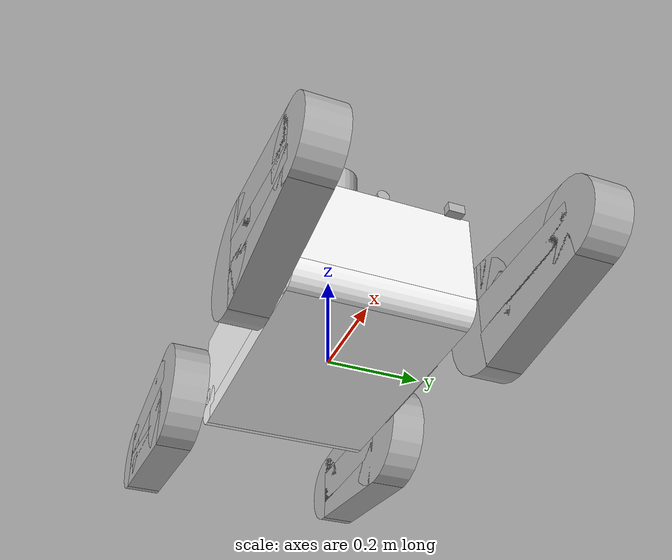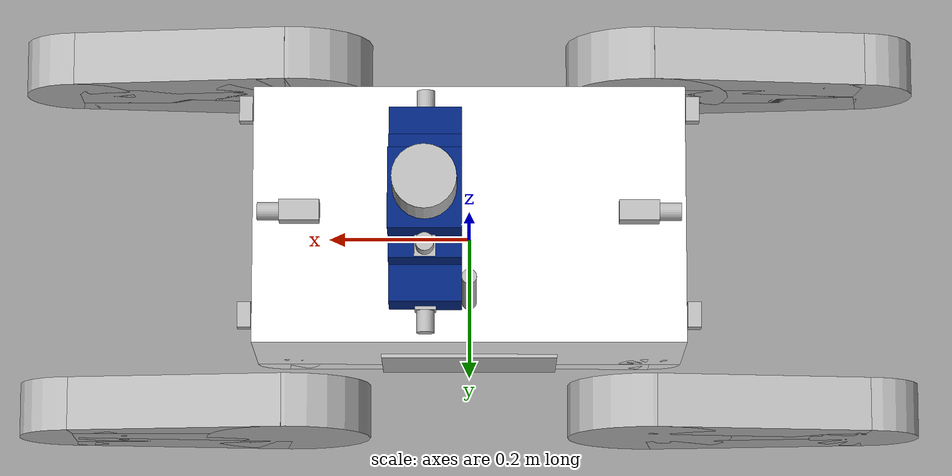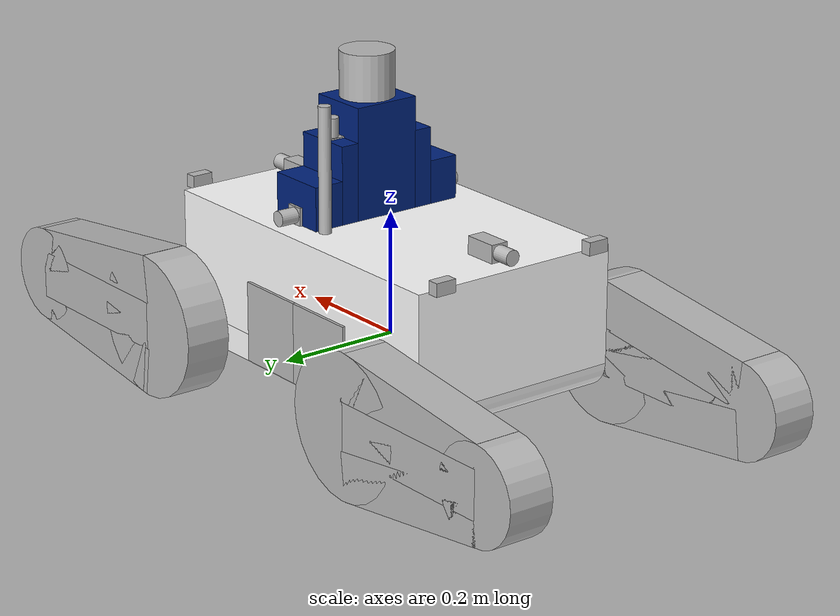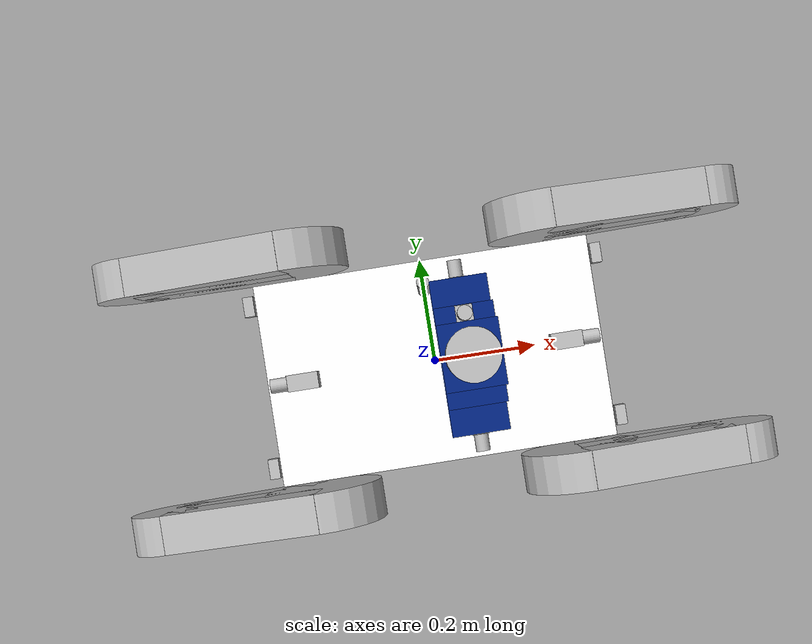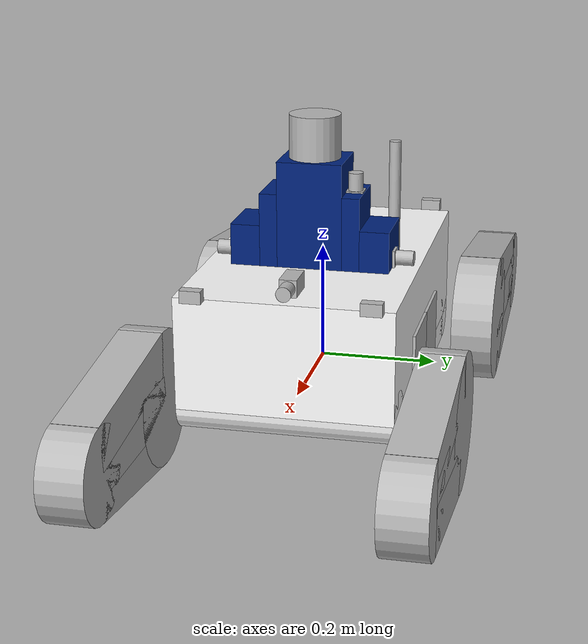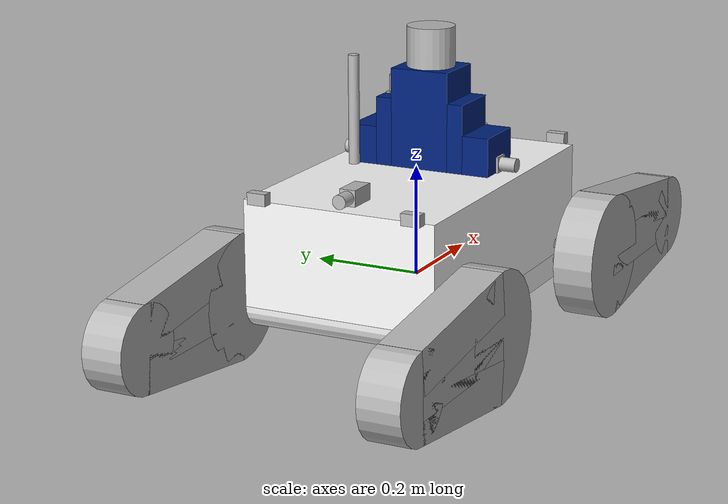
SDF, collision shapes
<?xml version='1.0' encoding='utf-8'?>
<sdf version="1.6">
  <model name="marv">
    <link name="base_link">
      <inertial>
        <pose>0 0 0.0661 0 -0 0</pose>
        <mass>8.7</mass>
        <inertia>
          <ixx>0.12905</ixx>
          <ixy>0</ixy>
          <ixz>0</ixz>
          <iyy>0.29609</iyy>
          <iyz>0</iyz>
          <izz>0.35496</izz>
        </inertia>
      </inertial>
      <collision name="base_link_collision">
        <pose>0 0 0.0961 0 -0 0</pose>
        <geometry>
          <box>
            <size>0.6 0.36 0.192</size>
          </box>
        </geometry>
      </collision>
      <collision name="base_link_collision_1">
        <pose>0 0 -0.0219 0 -0 0</pose>
        <geometry>
          <box>
            <size>0.512 0.36 0.044</size>
          </box>
        </geometry>
      </collision>
      <collision name="base_link_collision_2">
        <pose>0.256 0 0.000144 1.5707963267948966 -0 0</pose>
        <geometry>
          <cylinder>
            <length>0.36</length>
            <radius>0.044044</radius>
          </cylinder>
        </geometry>
      </collision>
      <collision name="base_link_collision_3">
        <pose>-0.256 0 0.000144 1.5707963267948966 -0 0</pose>
        <geometry>
          <cylinder>
            <length>0.36</length>
            <radius>0.044044</radius>
          </cylinder>
        </geometry>
      </collision>
      <visual name="base_link_fixed_joint_lump__chassis_visual">
        <material>
          <diffuse>1 1 1 1</diffuse>
          <pbr>
            <metal>
              <albedo_map>#{path}/textures/chassis.png</albedo_map>
              <emissive_map>#{path}/textures/chassis_emissive.png</emissive_map>
            </metal>
          </pbr>
        </material>
        <geometry>
          <mesh>
            <uri>#{path}/meshes/chassis.dae</uri>
          </mesh>
        </geometry>
      </visual>
      <visual name="base_link_visual_1">

        <pose>0 0 0.1841 0 -0 0</pose>
        <geometry>
          <mesh>
            <uri>#{path}/meshes/deck.dae</uri>
          </mesh>
        </geometry>
      </visual>
      <visual name="base_link_visual_2">

        <pose>0.256 0.18 0 0 -0 0</pose>
        <geometry>
          <mesh>
            <uri>#{path}/meshes/motor_housing.dae</uri>
          </mesh>
        </geometry>
      </visual>
      <visual name="base_link_visual_3">

        <pose>0.256 -0.18 0 0 -0 0</pose>
        <geometry>
          <mesh>
            <uri>#{path}/meshes/motor_housing_mirrored.dae</uri>
          </mesh>
        </geometry>
      </visual>
      <visual name="base_link_visual_4">

        <pose>-0.256 0.18 0 0 -0 0</pose>
        <geometry>
          <mesh>
            <scale>-1 -1 1</scale>
            <uri>#{path}/meshes/motor_housing_mirrored.dae</uri>
          </mesh>
        </geometry>
      </visual>
      <visual name="base_link_visual_5">
        <pose>-0.256 -0.18 0 0 -0 0</pose>
        <geometry>
          <mesh>
            <scale>-1 -1 1</scale>
            <uri>#{path}/meshes/motor_housing.dae</uri>
          </mesh>
        </geometry>
      </visual>
      <self_collide>0</self_collide>
      <light name="light_left" type="spot">
       <visualize>false</visualize>
        <pose>0 0.18 0.1621 1.5707963267948966 1.5707963267948966 0</pose>
        <cast_shadows>1</cast_shadows>
        <attenuation>
          <range>30</range>
          <linear>0.2</linear>
          <constant>0.1</constant>
          <quadratic>0.0025</quadratic>
        </attenuation>
        <diffuse>0.8 0.8 0.5 1</diffuse>
        <specular>0.8 0.8 0.5 1</specular>
        <spot>
          <inner_angle>2.8</inner_angle>
          <outer_angle>2.9</outer_angle>
          <falloff>1</falloff>
        </spot>
        <direction>1 0 0</direction>
      </light>
      <light name="light_right" type="spot">
       <visualize>false</visualize>
        <pose>0 -0.18 0.1621 -1.5707963267948966 1.5707963267948966 0</pose>
        <cast_shadows>1</cast_shadows>
        <attenuation>
          <range>30</range>
          <linear>0.2</linear>
          <constant>0.1</constant>
          <quadratic>0.0025</quadratic>
        </attenuation>
        <diffuse>0.8 0.8 0.5 1</diffuse>
        <specular>0.8 0.8 0.5 1</specular>
        <spot>
          <inner_angle>2.8</inner_angle>
          <outer_angle>2.9</outer_angle>
          <falloff>1</falloff>
        </spot>
        <direction>1 0 0</direction>
      </light>
      <light name="light_front" type="spot">
       <visualize>false</visualize>
        <pose>0.3 0 0.1621 -3.1415926535897931 1.5707963267948966 0</pose>
        <cast_shadows>1</cast_shadows>
        <attenuation>
          <range>30</range>
          <linear>0.2</linear>
          <constant>0.1</constant>
          <quadratic>0.0025</quadratic>
        </attenuation>
        <diffuse>0.8 0.8 0.5 1</diffuse>
        <specular>0.8 0.8 0.5 1</specular>
        <spot>
          <inner_angle>2.8</inner_angle>
          <outer_angle>2.9</outer_angle>
          <falloff>1</falloff>
        </spot>
        <direction>1 0 0</direction>
      </light>
      <light name="light_rear" type="spot">
       <visualize>false</visualize>
        <pose>-0.3 0 0.1621 0 1.5707963267948966 0</pose>
        <cast_shadows>1</cast_shadows>
        <attenuation>
          <range>40</range>
          <linear>0</linear>
          <constant>0.2</constant>
          <quadratic>0.0025</quadratic>
        </attenuation>
        <diffuse>0.8 0.8 0.5 1</diffuse>
        <specular>0.8 0.8 0.5 1</specular>
        <spot>
          <inner_angle>2.8</inner_angle>
          <outer_angle>2.9</outer_angle>
          <falloff>1</falloff>
        </spot>
        <direction>1 0 0</direction>
      </light>
    </link>
    <link name="battery1">
      <pose>0.06 0.005 0.0251 0 -0 0</pose>
      <inertial>
        <mass>6</mass>
        <inertia>
          <ixx>0.07325</ixx>
          <ixy>0</ixy>
          <ixz>0</ixz>
          <iyy>0.016388</iyy>
          <iyz>0</iyz>
          <izz>0.072738</izz>
        </inertia>
      </inertial>
      <collision name="battery1_collision">
        <geometry>
          <box>
            <size>0.126 0.36 0.13</size>
          </box>
        </geometry>
      </collision>
      <visual name="battery1_visual">
        <geometry>
          <mesh>
            <uri>#{path}/meshes/battery.dae</uri>
          </mesh>
        </geometry>
      </visual>
    </link>
    <joint name="battery1_j" type="fixed">
      <child>battery1</child>
      <parent>base_link</parent>
      <axis>
        <dynamics>
          <spring_reference>0</spring_reference>
          <spring_stiffness>0</spring_stiffness>
        </dynamics>
        <xyz>0 0 1</xyz>
        <use_parent_model_frame>0</use_parent_model_frame>
        <limit>
          <lower>-1e+16</lower>
          <upper>1e+16</upper>
        </limit>
      </axis>
      <physics>
        <ode>
          <limit>
            <cfm>0</cfm>
            <erp>0.2</erp>
          </limit>
        </ode>
      </physics>
    </joint>
    <link name="battery2">
      <pose>-0.06 0.005 0.0251 0 -0 0</pose>
      <inertial>
        <mass>6</mass>
        <inertia>
          <ixx>0.07325</ixx>
          <ixy>0</ixy>
          <ixz>0</ixz>
          <iyy>0.016388</iyy>
          <iyz>0</iyz>
          <izz>0.072738</izz>
        </inertia>
      </inertial>
      <collision name="battery2_collision">
        <geometry>
          <box>
            <size>0.126 0.36 0.13</size>
          </box>
        </geometry>
      </collision>
      <visual name="battery2_visual">
        <geometry>
          <mesh>
            <uri>#{path}/meshes/battery.dae</uri>
          </mesh>
        </geometry>
      </visual>
    </link>
    <joint name="battery2_j" type="fixed">
      <child>battery2</child>
      <parent>base_link</parent>
      <axis>
        <dynamics>
          <spring_reference>0</spring_reference>
          <spring_stiffness>0</spring_stiffness>
        </dynamics>
        <xyz>0 0 1</xyz>
        <use_parent_model_frame>0</use_parent_model_frame>
        <limit>
          <lower>-1e+16</lower>
          <upper>1e+16</upper>
        </limit>
      </axis>
      <physics>
        <ode>
          <limit>
            <cfm>0</cfm>
            <erp>0.2</erp>
          </limit>
        </ode>
      </physics>
    </joint>
    <link name="bottom_plate">
      <inertial>
        <pose>0 0 -0.0439 0 -0 0</pose>
        <mass>1.09</mass>
        <inertia>
          <ixx>0.0117743</ixx>
          <ixy>0</ixy>
          <ixz>0</ixz>
          <iyy>0.0327023</iyy>
          <iyz>0</iyz>
          <izz>0.044472</izz>
        </inertia>
      </inertial>
    </link>
    <joint name="bottom_plate_j" type="fixed">
      <child>bottom_plate</child>
      <parent>base_link</parent>
      <axis>
        <dynamics>
          <spring_reference>0</spring_reference>
          <spring_stiffness>0</spring_stiffness>
        </dynamics>
        <xyz>0 0 1</xyz>
        <use_parent_model_frame>0</use_parent_model_frame>
        <limit>
          <lower>-1e+16</lower>
          <upper>1e+16</upper>
        </limit>
      </axis>
      <physics>
        <ode>
          <limit>
            <cfm>0</cfm>
            <erp>0.2</erp>
          </limit>
        </ode>
      </physics>
    </joint>
    <link name="deck">
      <inertial>
        <pose>0 0 0.1921 0 -0 0</pose>
        <mass>3.4</mass>
        <inertia>
          <ixx>0.0367925</ixx>
          <ixy>0</ixy>
          <ixz>0</ixz>
          <iyy>0.102073</iyy>
          <iyz>0</iyz>
          <izz>0.13872</izz>
        </inertia>
      </inertial>
    </link>
    <joint name="deck_j" type="fixed">
      <child>deck</child>
      <parent>base_link</parent>
      <axis>
        <dynamics>
          <spring_reference>0</spring_reference>
          <spring_stiffness>0</spring_stiffness>
        </dynamics>
        <xyz>0 0 1</xyz>
        <use_parent_model_frame>0</use_parent_model_frame>
        <limit>
          <lower>-1e+16</lower>
          <upper>1e+16</upper>
        </limit>
      </axis>
      <physics>
        <ode>
          <limit>
            <cfm>0</cfm>
            <erp>0.2</erp>
          </limit>
        </ode>
      </physics>
    </joint>
    <link name="front_cam">
      <pose>0.244 0 0.1321 0 -0 0</pose>
      <inertial>
        <pose>0.019862 0 0.0145 0 -0 0</pose>
        <mass>0.14</mass>
        <inertia>
          <ixx>1.96233e-05</ixx>
          <ixy>0</ixy>
          <ixz>0</ixz>
          <iyy>6.75088e-05</iyy>
          <iyz>0</iyz>
          <izz>6.75088e-05</izz>
        </inertia>
      </inertial>
      <collision name="front_cam_collision_collision">
        <pose>0.0117 0 0.0145 0 -0 0</pose>
        <geometry>
          <box>
            <size>0.054 0.029 0.029</size>
          </box>
        </geometry>
      </collision>
      <collision name="front_cam_lens_collision_collision_1">
        <pose>0.042024 0 0.0145 0 1.5707963267948966 0</pose>
        <geometry>
          <cylinder>
            <length>0.026</length>
            <radius>0.0125</radius>
          </cylinder>
        </geometry>
      </collision>
      <visual name="front_cam_visual">
        <pose>0 0 0.0145 0 -0 0</pose>
        <geometry>
          <mesh>
            <uri>#{path}/meshes/basler_ace.dae</uri>
          </mesh>
        </geometry>
      </visual>
      <visual name="front_cam_visual_1">
        <pose>0.029024 0 0.0145 0 -0 0</pose>
        <geometry>
          <mesh>
            <uri>#{path}/meshes/evetar_fisheye_lens.dae</uri>
          </mesh>
        </geometry>
      </visual>
      <sensor name="front_cam" type="camera">
        <pose>0.051574 0 0.0145 0 -0 0</pose>
        <update_rate>15</update_rate>
        <camera>
          <horizontal_fov>2.40855</horizontal_fov>
          <image>
            <width>2048</width>
            <height>1536</height>
            <format>R8G8B8</format>
          </image>
          <clip>
            <near>0.025</near>
            <far>300</far>
          </clip>
          <noise>
            <type>gaussian</type>
            <mean>0</mean>
            <stddev>0.007</stddev>
          </noise>
          <lens>
            <intrinsics>
              <fx>393.077</fx>
              <fy>393.077</fy>
              <cx>1023.5</cx>
              <cy>767.5</cy>
              <s>0</s>
            </intrinsics>
            <type>stereographic</type>
            <scale_to_hfov>1</scale_to_hfov>
          </lens>
        </camera>
      </sensor>
    </link>
    <joint name="front_cam_j" type="fixed">
      <child>front_cam</child>
      <parent>base_link</parent>
      <axis>
        <dynamics>
          <spring_reference>0</spring_reference>
          <spring_stiffness>0</spring_stiffness>
        </dynamics>
        <xyz>0 0 1</xyz>
        <use_parent_model_frame>0</use_parent_model_frame>
        <limit>
          <lower>-1e+16</lower>
          <upper>1e+16</upper>
        </limit>
      </axis>
      <physics>
        <ode>
          <limit>
            <cfm>0</cfm>
            <erp>0.2</erp>
          </limit>
        </ode>
      </physics>
    </joint>
    <link name="front_left_flipper">
      <pose>0.256 0.248 0 0 -0 0</pose>
      <inertial>
        <mass>1e-05</mass>
        <inertia>
          <ixx>0.001</ixx>
          <ixy>1e-06</ixy>
          <ixz>1e-06</ixz>
          <iyy>0.001</iyy>
          <iyz>1e-06</iyz>
          <izz>0.001</izz>
        </inertia>
      </inertial>
      <collision name="front_left_flipper_collision">
          <pose>0.15175 0 0 0 -0 0</pose>
          <geometry>
            <box>
              <size>0.3035 0.075 0.078</size>
            </box>
          </geometry>
          <surface>
            <friction>
              <ode>
                <mu>1</mu>
                <mu2>150</mu2>
                <fdir1>0 0 1</fdir1>
              </ode>
            </friction>
          </surface>
        </collision>
        <collision name="front_left_flipper_collision_1">
          <pose>0.15175 0 0.05825 0 0.126179 0</pose>
          <geometry>
            <box>
              <size>0.3035 0.075 0.078</size>
            </box>
          </geometry>
          <surface>
            <friction>
              <ode>
                <mu>1</mu>
                <mu2>150</mu2>
                <fdir1>0 0 1</fdir1>
              </ode>
            </friction>
          </surface>
        </collision>
        <collision name="front_left_flipper_collision_2">
          <pose>0.15175 0 -0.05825 0 -0.126179 0</pose>
          <geometry>
            <box>
              <size>0.3035 0.075 0.078</size>
            </box>
          </geometry>
          <surface>
            <friction>
              <ode>
                <mu>1</mu>
                <mu2>150</mu2>
                <fdir1>0 0 1</fdir1>
              </ode>
            </friction>
          </surface>
        </collision>
        <collision name="front_left_flipper_collision_3">
          <pose>0.3035 0 0 1.5707963267948966 -0 0</pose>
          <geometry>
            <cylinder>
              <length>0.075</length>
              <radius>0.078</radius>
            </cylinder>
          </geometry>
          <surface>
            <friction>
              <ode>
                <mu>1</mu>
                <mu2>150</mu2>
                <fdir1>0 0 1</fdir1>
              </ode>
            </friction>
          </surface>
        </collision>
        <collision name="front_left_flipper_collision_4">
          <pose>0 0 0 1.5707963267948966 -0 0</pose>
          <geometry>
            <cylinder>
              <length>0.075</length>
              <radius>0.1165</radius>
            </cylinder>
          </geometry>
          <surface>
            <friction>
              <ode>
                <mu>1</mu>
                <mu2>150</mu2>
                <fdir1>0 0 1</fdir1>
              </ode>
            </friction>
          </surface>
        </collision>
      <visual name="front_left_flipper_visual">

        <geometry>
          <mesh>
            <uri>#{path}/meshes/big_wheel.dae</uri>
          </mesh>
        </geometry>
      </visual>
      <visual name="front_left_flipper_visual_1">

        <geometry>
          <mesh>
            <scale>-1 -1 1</scale>
            <uri>#{path}/meshes/flipper_arm.dae</uri>
          </mesh>
        </geometry>
      </visual>
      <visual name="front_left_flipper_visual_2">

        <geometry>
          <mesh>
            <uri>#{path}/meshes/belt.dae</uri>
          </mesh>
        </geometry>
      </visual>
      <visual name="front_left_flipper_visual_3">

        <pose>0.3035 0 0 0 -0 0</pose>
        <geometry>
          <mesh>
            <uri>#{path}/meshes/small_wheel.dae</uri>
          </mesh>
        </geometry>
      </visual>
      <self_collide>1</self_collide>
    </link>
    <joint name="front_left_flipper_j" type="revolute">
      <child>front_left_flipper</child>
      <parent>base_link</parent>
      <axis>
        <xyz>0 1 0</xyz>
        <limit>
          <lower>-1e+16</lower>
          <upper>1e+16</upper>
          <effort>240</effort>
          <velocity>5</velocity>
        </limit>
        <dynamics>
          <spring_reference>0</spring_reference>
          <spring_stiffness>0</spring_stiffness>
        </dynamics>
        <use_parent_model_frame>0</use_parent_model_frame>
      </axis>
      <physics>
        <ode>
          <implicit_spring_damper>1</implicit_spring_damper>
          <cfm_damping>1</cfm_damping>
          <limit>
            <cfm>0</cfm>
            <erp>0.2</erp>
          </limit>
        </ode>
      </physics>
    </joint>
    <link name="front_left_flipper_end_point_inflated">
      <pose>0.6375 0.248 0 0 -0 0</pose>
      <inertial>
        <mass>1e-05</mass>
        <inertia>
          <ixx>0.001</ixx>
          <ixy>1e-06</ixy>
          <ixz>1e-06</ixz>
          <iyy>0.001</iyy>
          <iyz>1e-06</iyz>
          <izz>0.001</izz>
        </inertia>
      </inertial>
    </link>
    <joint name="front_left_flipper_end_point_inflated_j" type="fixed">
      <child>front_left_flipper_end_point_inflated</child>
      <parent>front_left_flipper</parent>
      <axis>
        <dynamics>
          <spring_reference>0</spring_reference>
          <spring_stiffness>0</spring_stiffness>
        </dynamics>
        <xyz>0 0 1</xyz>
        <use_parent_model_frame>0</use_parent_model_frame>
        <limit>
          <lower>-1e+16</lower>
          <upper>1e+16</upper>
        </limit>
      </axis>
      <physics>
        <ode>
          <limit>
            <cfm>0</cfm>
            <erp>0.2</erp>
          </limit>
        </ode>
      </physics>
    </joint>
    <link name="front_left_flipper_end_point">
      <pose>0.6375 0.248 0 0 -0 0</pose>
      <inertial>
        <mass>1e-05</mass>
        <inertia>
          <ixx>0.001</ixx>
          <ixy>1e-06</ixy>
          <ixz>1e-06</ixz>
          <iyy>0.001</iyy>
          <iyz>1e-06</iyz>
          <izz>0.001</izz>
        </inertia>
      </inertial>
    </link>
    <joint name="front_left_flipper_end_point_j" type="fixed">
      <child>front_left_flipper_end_point</child>
      <parent>front_left_flipper</parent>
      <axis>
        <dynamics>
          <spring_reference>0</spring_reference>
          <spring_stiffness>0</spring_stiffness>
        </dynamics>
        <xyz>0 0 1</xyz>
        <use_parent_model_frame>0</use_parent_model_frame>
        <limit>
          <lower>-1e+16</lower>
          <upper>1e+16</upper>
        </limit>
      </axis>
      <physics>
        <ode>
          <limit>
            <cfm>0</cfm>
            <erp>0.2</erp>
          </limit>
        </ode>
      </physics>
    </joint>
    <link name="front_left_motor">
      <inertial>
        <pose>0.22 -0.09 0.02 0 -0 0</pose>
        <mass>4.06</mass>
        <inertia>
          <ixx>0.0151492</ixx>
          <ixy>0</ixy>
          <ixz>0</ixz>
          <iyy>0.0129839</iyy>
          <iyz>0</iyz>
          <izz>0.0173903</izz>
        </inertia>
      </inertial>
    </link>
    <joint name="front_left_motor_j" type="fixed">
      <child>front_left_motor</child>
      <parent>base_link</parent>
      <axis>
        <dynamics>
          <spring_reference>0</spring_reference>
          <spring_stiffness>0</spring_stiffness>
        </dynamics>
        <xyz>0 0 1</xyz>
        <use_parent_model_frame>0</use_parent_model_frame>
        <limit>
          <lower>-1e+16</lower>
          <upper>1e+16</upper>
        </limit>
      </axis>
      <physics>
        <ode>
          <limit>
            <cfm>0</cfm>
            <erp>0.2</erp>
          </limit>
        </ode>
      </physics>
    </joint>
    <link name="front_right_flipper">
      <pose>0.256 -0.248 0 3.1415926535897931 -0 -3.1415926535897931</pose>
      <inertial>
        <mass>1e-05</mass>
        <inertia>
          <ixx>0.001</ixx>
          <ixy>1e-06</ixy>
          <ixz>1e-06</ixz>
          <iyy>0.001</iyy>
          <iyz>1e-06</iyz>
          <izz>0.001</izz>
        </inertia>
      </inertial>
      <collision name="front_right_flipper_collision">
          <pose>-0.15175 0 0 0 -0 0</pose>
          <geometry>
            <box>
              <size>0.3035 0.075 0.078</size>
            </box>
          </geometry>
          <surface>
            <friction>
              <ode>
                <mu>1</mu>
                <mu2>150</mu2>
                <fdir1>0 0 1</fdir1>
              </ode>
            </friction>
          </surface>
        </collision>
        <collision name="front_right_flipper_collision_1">
          <pose>-0.15175 0 0.05825 0 -0.126179 0</pose>
          <geometry>
            <box>
              <size>0.3035 0.075 0.078</size>
            </box>
          </geometry>
          <surface>
            <friction>
              <ode>
                <mu>1</mu>
                <mu2>150</mu2>
                <fdir1>0 0 1</fdir1>
              </ode>
            </friction>
          </surface>
        </collision>
        <collision name="front_right_flipper_collision_2">
          <pose>-0.15175 0 -0.05825 0 0.126179 0</pose>
          <geometry>
            <box>
              <size>0.3035 0.075 0.078</size>
            </box>
          </geometry>
          <surface>
            <friction>
              <ode>
                <mu>1</mu>
                <mu2>150</mu2>
                <fdir1>0 0 1</fdir1>
              </ode>
            </friction>
          </surface>
        </collision>
        <collision name="front_right_flipper_collision_3">
          <pose>-0.3035 0 0 1.5707963267948966 -0 0</pose>
          <geometry>
            <cylinder>
              <length>0.075</length>
              <radius>0.078</radius>
            </cylinder>
          </geometry>
          <surface>
            <friction>
              <ode>
                <mu>1</mu>
                <mu2>150</mu2>
                <fdir1>0 0 1</fdir1>
              </ode>
            </friction>
          </surface>
        </collision>
        <collision name="front_right_flipper_collision_4">
          <pose>0 0 0 1.5707963267948966 -0 0</pose>
          <geometry>
            <cylinder>
              <length>0.075</length>
              <radius>0.1165</radius>
            </cylinder>
          </geometry>
          <surface>
            <friction>
              <ode>
                <mu>1</mu>
                <mu2>150</mu2>
                <fdir1>0 0 1</fdir1>
              </ode>
            </friction>
          </surface>
        </collision>
      <visual name="front_right_flipper_visual">
        <geometry>
          <mesh>
            <uri>#{path}/meshes/big_wheel.dae</uri>
          </mesh>
        </geometry>
      </visual>
      <visual name="front_right_flipper_visual_1">
        <geometry>
          <mesh>
            <uri>#{path}/meshes/flipper_arm.dae</uri>
          </mesh>
        </geometry>
      </visual>
      <visual name="front_right_flipper_visual_2">
        <pose>0 0 0 3.1415926535897931 -0 3.1415926535897931</pose>
        <geometry>
          <mesh>
            <uri>#{path}/meshes/belt.dae</uri>
          </mesh>
        </geometry>
      </visual>
      <visual name="front_right_flipper_visual_3">
        <pose>-0.3035 0 0 0 -0 0</pose>
        <geometry>
          <mesh>
            <uri>#{path}/meshes/small_wheel.dae</uri>
          </mesh>
        </geometry>
      </visual>
      <self_collide>1</self_collide>
    </link>
    <joint name="front_right_flipper_j" type="revolute">
      <child>front_right_flipper</child>
      <parent>base_link</parent>
      <axis>
        <xyz>0 1 0</xyz>
        <limit>
          <lower>-1e+16</lower>
          <upper>1e+16</upper>
          <effort>240</effort>
          <velocity>5</velocity>
        </limit>
        <dynamics>
          <spring_reference>0</spring_reference>
          <spring_stiffness>0</spring_stiffness>
        </dynamics>
        <use_parent_model_frame>0</use_parent_model_frame>
      </axis>
      <physics>
        <ode>
          <implicit_spring_damper>1</implicit_spring_damper>
          <cfm_damping>1</cfm_damping>
          <limit>
            <cfm>0</cfm>
            <erp>0.2</erp>
          </limit>
        </ode>
      </physics>
    </joint>
    <link name="front_right_flipper_end_point_inflated">
      <pose>0.6375 -0.248 -0 3.1415926535897931 -0 3.1415926535897931</pose>
      <inertial>
        <mass>1e-05</mass>
        <inertia>
          <ixx>0.001</ixx>
          <ixy>1e-06</ixy>
          <ixz>1e-06</ixz>
          <iyy>0.001</iyy>
          <iyz>1e-06</iyz>
          <izz>0.001</izz>
        </inertia>
      </inertial>
    </link>
    <joint name="front_right_flipper_end_point_inflated_j" type="fixed">
      <child>front_right_flipper_end_point_inflated</child>
      <parent>front_right_flipper</parent>
      <axis>
        <dynamics>
          <spring_reference>0</spring_reference>
          <spring_stiffness>0</spring_stiffness>
        </dynamics>
        <xyz>0 0 1</xyz>
        <use_parent_model_frame>0</use_parent_model_frame>
        <limit>
          <lower>-1e+16</lower>
          <upper>1e+16</upper>
        </limit>
      </axis>
      <physics>
        <ode>
          <limit>
            <cfm>0</cfm>
            <erp>0.2</erp>
          </limit>
        </ode>
      </physics>
    </joint>
    <link name="front_right_flipper_end_point">
      <pose>0.6375 -0.248 -0 3.1415926535897931 -0 3.1415926535897931</pose>
      <inertial>
        <mass>1e-05</mass>
        <inertia>
          <ixx>0.001</ixx>
          <ixy>1e-06</ixy>
          <ixz>1e-06</ixz>
          <iyy>0.001</iyy>
          <iyz>1e-06</iyz>
          <izz>0.001</izz>
        </inertia>
      </inertial>
    </link>
    <joint name="front_right_flipper_end_point_j" type="fixed">
      <child>front_right_flipper_end_point</child>
      <parent>front_right_flipper</parent>
      <axis>
        <dynamics>
          <spring_reference>0</spring_reference>
          <spring_stiffness>0</spring_stiffness>
        </dynamics>
        <xyz>0 0 1</xyz>
        <use_parent_model_frame>0</use_parent_model_frame>
        <limit>
          <lower>-1e+16</lower>
          <upper>1e+16</upper>
        </limit>
      </axis>
      <physics>
        <ode>
          <limit>
            <cfm>0</cfm>
            <erp>0.2</erp>
          </limit>
        </ode>
      </physics>
    </joint>
    <link name="front_right_motor">
      <inertial>
        <pose>0.22 0.09 0.02 0 -0 0</pose>
        <mass>4.06</mass>
        <inertia>
          <ixx>0.0151492</ixx>
          <ixy>0</ixy>
          <ixz>0</ixz>
          <iyy>0.0129839</iyy>
          <iyz>0</iyz>
          <izz>0.0173903</izz>
        </inertia>
      </inertial>
    </link>
    <joint name="front_right_motor_j" type="fixed">
      <child>front_right_motor</child>
      <parent>base_link</parent>
      <axis>
        <dynamics>
          <spring_reference>0</spring_reference>
          <spring_stiffness>0</spring_stiffness>
        </dynamics>
        <xyz>0 0 1</xyz>
        <use_parent_model_frame>0</use_parent_model_frame>
        <limit>
          <lower>-1e+16</lower>
          <upper>1e+16</upper>
        </limit>
      </axis>
      <physics>
        <ode>
          <limit>
            <cfm>0</cfm>
            <erp>0.2</erp>
          </limit>
        </ode>
      </physics>
    </joint>
    <link name="imu">
      <pose>0 0 0.15 -3.1415926535897931 0 0</pose>
      <inertial>
        <mass>1e-05</mass>
        <inertia>
          <ixx>0.001</ixx>
          <ixy>1e-06</ixy>
          <ixz>1e-06</ixz>
          <iyy>0.001</iyy>
          <iyz>1e-06</iyz>
          <izz>0.001</izz>
        </inertia>
      </inertial>
      <self_collide>0</self_collide>
      <sensor name="imu" type="imu">
        <always_on>1</always_on>
        <update_rate>50</update_rate>
        <imu>
          <angular_velocity>
            <x>
              <noise type="gaussian">
                <mean>0</mean>
                <stddev>0.009</stddev>
                <bias_mean>0.00075</bias_mean>
                <bias_stddev>0.005</bias_stddev>
                <dynamic_bias_stddev>2e-05</dynamic_bias_stddev>
                <dynamic_bias_correlation_time>400</dynamic_bias_correlation_time>
                <precision>0.00025</precision>
              </noise>
            </x>
            <y>
              <noise type="gaussian">
                <mean>0</mean>
                <stddev>0.009</stddev>
                <bias_mean>0.00075</bias_mean>
                <bias_stddev>0.005</bias_stddev>
                <dynamic_bias_stddev>2e-05</dynamic_bias_stddev>
                <dynamic_bias_correlation_time>400</dynamic_bias_correlation_time>
                <precision>0.00025</precision>
              </noise>
            </y>
            <z>
              <noise type="gaussian">
                <mean>0</mean>
                <stddev>0.009</stddev>
                <bias_mean>0.00075</bias_mean>
                <bias_stddev>0.005</bias_stddev>
                <dynamic_bias_stddev>2e-05</dynamic_bias_stddev>
                <dynamic_bias_correlation_time>400</dynamic_bias_correlation_time>
                <precision>0.00025</precision>
              </noise>
            </z>
          </angular_velocity>
          <linear_acceleration>
            <x>
              <noise type="gaussian">
                <mean>0</mean>
                <stddev>0.021</stddev>
                <bias_mean>0.05</bias_mean>
                <bias_stddev>0.0075</bias_stddev>
                <dynamic_bias_stddev>0.000375</dynamic_bias_stddev>
                <dynamic_bias_correlation_time>175</dynamic_bias_correlation_time>
                <precision>0.005</precision>
              </noise>
            </x>
            <y>
              <noise type="gaussian">
                <mean>0</mean>
                <stddev>0.021</stddev>
                <bias_mean>0.05</bias_mean>
                <bias_stddev>0.0075</bias_stddev>
                <dynamic_bias_stddev>0.000375</dynamic_bias_stddev>
                <dynamic_bias_correlation_time>175</dynamic_bias_correlation_time>
                <precision>0.005</precision>
              </noise>
            </y>
            <z>
              <noise type="gaussian">
                <mean>0</mean>
                <stddev>0.021</stddev>
                <bias_mean>0.05</bias_mean>
                <bias_stddev>0.0075</bias_stddev>
                <dynamic_bias_stddev>0.000375</dynamic_bias_stddev>
                <dynamic_bias_correlation_time>175</dynamic_bias_correlation_time>
                <precision>0.005</precision>
              </noise>
            </z>
          </linear_acceleration>
        </imu>
      </sensor>
    </link>
    <joint name="imu_j" type="fixed">
      <child>imu</child>
      <parent>base_link</parent>
      <axis>
        <dynamics>
          <spring_reference>0</spring_reference>
          <spring_stiffness>0</spring_stiffness>
        </dynamics>
        <xyz>0 0 1</xyz>
        <use_parent_model_frame>0</use_parent_model_frame>
        <limit>
          <lower>-1e+16</lower>
          <upper>1e+16</upper>
        </limit>
      </axis>
      <physics>
        <ode>
          <limit>
            <cfm>0</cfm>
            <erp>0.2</erp>
          </limit>
        </ode>
      </physics>
    </joint>
    <link name="rear_cam">
      <pose>-0.244 0 0.1321 0 0 -3.1415926535897931</pose>
      <inertial>
        <pose>0.019862 0 0.0145 0 -0 0</pose>
        <mass>0.14</mass>
        <inertia>
          <ixx>1.96233e-05</ixx>
          <ixy>0</ixy>
          <ixz>0</ixz>
          <iyy>6.75088e-05</iyy>
          <iyz>0</iyz>
          <izz>6.75088e-05</izz>
        </inertia>
      </inertial>
      <collision name="rear_cam_collision_collision">
        <pose>0.0117 0 0.0145 0 -0 0</pose>
        <geometry>
          <box>
            <size>0.054 0.029 0.029</size>
          </box>
        </geometry>
      </collision>
      <collision name="rear_cam_lens_collision_collision_1">
        <pose>0.042024 0 0.0145 0 1.5707963267948966 0</pose>
        <geometry>
          <cylinder>
            <length>0.026</length>
            <radius>0.0125</radius>
          </cylinder>
        </geometry>
      </collision>
      <visual name="rear_cam_visual">
        <pose>0 0 0.0145 0 -0 0</pose>
        <geometry>
          <mesh>
            <uri>#{path}/meshes/basler_ace.dae</uri>
          </mesh>
        </geometry>
      </visual>
      <visual name="rear_cam_visual_1">
        <pose>0.029024 0 0.0145 0 -0 0</pose>
        <geometry>
          <mesh>
            <uri>#{path}/meshes/evetar_fisheye_lens.dae</uri>
          </mesh>
        </geometry>
      </visual>
      <sensor name="rear_cam" type="camera">
        <pose>0.051574 0 0.0145 0 -0 0</pose>
        <update_rate>15</update_rate>

        <camera>
          <horizontal_fov>2.40855</horizontal_fov>
          <image>
            <width>2048</width>
            <height>1536</height>
            <format>R8G8B8</format>
          </image>
          <clip>
            <near>0.025</near>
            <far>300</far>
          </clip>
          <noise>
            <type>gaussian</type>
            <mean>0</mean>
            <stddev>0.007</stddev>
          </noise>
          <lens>
            <intrinsics>
              <fx>393.077</fx>
              <fy>393.077</fy>
              <cx>1023.5</cx>
              <cy>767.5</cy>
              <s>0</s>
            </intrinsics>
            <type>stereographic</type>
            <scale_to_hfov>1</scale_to_hfov>
          </lens>
        </camera>
      </sensor>
    </link>
    <joint name="rear_cam_j" type="fixed">
      <child>rear_cam</child>
      <parent>base_link</parent>
      <axis>
        <dynamics>
          <spring_reference>0</spring_reference>
          <spring_stiffness>0</spring_stiffness>
        </dynamics>
        <xyz>0 0 1</xyz>
        <use_parent_model_frame>0</use_parent_model_frame>
        <limit>
          <lower>-1e+16</lower>
          <upper>1e+16</upper>
        </limit>
      </axis>
      <physics>
        <ode>
          <limit>
            <cfm>0</cfm>
            <erp>0.2</erp>
          </limit>
        </ode>
      </physics>
    </joint>
    <link name="rear_left_flipper">
      <pose>-0.256 0.248 0 3.1415926535897931 -0 -3.1415926535897931</pose>
      <inertial>
        <mass>1e-05</mass>
        <inertia>
          <ixx>0.001</ixx>
          <ixy>1e-06</ixy>
          <ixz>1e-06</ixz>
          <iyy>0.001</iyy>
          <iyz>1e-06</iyz>
          <izz>0.001</izz>
        </inertia>
      </inertial>
      <collision name="rear_left_flipper_collision">
          <pose>0.15175 0 0 0 -0 0</pose>
          <geometry>
            <box>
              <size>0.3035 0.075 0.078</size>
            </box>
          </geometry>
          <surface>
            <friction>
              <ode>
                <mu>1</mu>
                <mu2>150</mu2>
                <fdir1>0 0 1</fdir1>
              </ode>
            </friction>
          </surface>
        </collision>
        <collision name="rear_left_flipper_collision_1">
          <pose>0.15175 0 0.05825 0 0.126179 0</pose>
          <geometry>
            <box>
              <size>0.3035 0.075 0.078</size>
            </box>
          </geometry>
          <surface>
            <friction>
              <ode>
                <mu>1</mu>
                <mu2>150</mu2>
                <fdir1>0 0 1</fdir1>
              </ode>
            </friction>
          </surface>
        </collision>
        <collision name="rear_left_flipper_collision_2">
          <pose>0.15175 0 -0.05825 0 -0.126179 0</pose>
          <geometry>
            <box>
              <size>0.3035 0.075 0.078</size>
            </box>
          </geometry>
          <surface>
            <friction>
              <ode>
                <mu>1</mu>
                <mu2>150</mu2>
                <fdir1>0 0 1</fdir1>
              </ode>
            </friction>
          </surface>
        </collision>
        <collision name="rear_left_flipper_collision_3">
          <pose>0.3035 0 0 1.5707963267948966 -0 0</pose>
          <geometry>
            <cylinder>
              <length>0.075</length>
              <radius>0.078</radius>
            </cylinder>
          </geometry>
          <surface>
            <friction>
              <ode>
                <mu>1</mu>
                <mu2>150</mu2>
                <fdir1>0 0 1</fdir1>
              </ode>
            </friction>
          </surface>
        </collision>
        <collision name="rear_left_flipper_collision_4">
          <pose>0 0 0 1.5707963267948966 -0 0</pose>
          <geometry>
            <cylinder>
              <length>0.075</length>
              <radius>0.1165</radius>
            </cylinder>
          </geometry>
          <surface>
            <friction>
              <ode>
                <mu>1</mu>
                <mu2>150</mu2>
                <fdir1>0 0 1</fdir1>
              </ode>
            </friction>
          </surface>
        </collision>
      <visual name="rear_left_flipper_visual">
        <geometry>
          <mesh>
            <uri>#{path}/meshes/big_wheel.dae</uri>
          </mesh>
        </geometry>
      </visual>
      <visual name="rear_left_flipper_visual_1">
        <geometry>
          <mesh>
            <scale>-1 -1 1</scale>
            <uri>#{path}/meshes/flipper_arm.dae</uri>
          </mesh>
        </geometry>
      </visual>
      <visual name="rear_left_flipper_visual_2">
        <geometry>
          <mesh>
            <uri>#{path}/meshes/belt.dae</uri>
          </mesh>
        </geometry>
      </visual>
      <visual name="rear_left_flipper_visual_3">
        <pose>0.3035 0 0 0 -0 0</pose>
        <geometry>
          <mesh>
            <uri>#{path}/meshes/small_wheel.dae</uri>
          </mesh>
        </geometry>
      </visual>
      <self_collide>1</self_collide>
    </link>
    <joint name="rear_left_flipper_j" type="revolute">
      <child>rear_left_flipper</child>
      <parent>base_link</parent>
      <axis>
        <xyz>0 1 0</xyz>
        <limit>
          <lower>-1e+16</lower>
          <upper>1e+16</upper>
          <effort>240</effort>
          <velocity>5</velocity>
        </limit>
        <dynamics>
          <spring_reference>0</spring_reference>
          <spring_stiffness>0</spring_stiffness>
        </dynamics>
        <use_parent_model_frame>0</use_parent_model_frame>
      </axis>
      <physics>
        <ode>
          <implicit_spring_damper>1</implicit_spring_damper>
          <cfm_damping>1</cfm_damping>
          <limit>
            <cfm>0</cfm>
            <erp>0.2</erp>
          </limit>
        </ode>
      </physics>
    </joint>
    <link name="rear_left_flipper_end_point_inflated">
      <pose>-0.6375 0.248 0 3.1415926535897931 -0 3.1415926535897931</pose>
      <inertial>
        <mass>1e-05</mass>
        <inertia>
          <ixx>0.001</ixx>
          <ixy>1e-06</ixy>
          <ixz>1e-06</ixz>
          <iyy>0.001</iyy>
          <iyz>1e-06</iyz>
          <izz>0.001</izz>
        </inertia>
      </inertial>
    </link>
    <joint name="rear_left_flipper_end_point_inflated_j" type="fixed">
      <child>rear_left_flipper_end_point_inflated</child>
      <parent>rear_left_flipper</parent>
      <axis>
        <dynamics>
          <spring_reference>0</spring_reference>
          <spring_stiffness>0</spring_stiffness>
        </dynamics>
        <xyz>0 0 1</xyz>
        <use_parent_model_frame>0</use_parent_model_frame>
        <limit>
          <lower>-1e+16</lower>
          <upper>1e+16</upper>
        </limit>
      </axis>
      <physics>
        <ode>
          <limit>
            <cfm>0</cfm>
            <erp>0.2</erp>
          </limit>
        </ode>
      </physics>
    </joint>
    <link name="rear_left_flipper_end_point">
      <pose>-0.6375 0.248 0 3.1415926535897931 -0 3.1415926535897931</pose>
      <inertial>
        <mass>1e-05</mass>
        <inertia>
          <ixx>0.001</ixx>
          <ixy>1e-06</ixy>
          <ixz>1e-06</ixz>
          <iyy>0.001</iyy>
          <iyz>1e-06</iyz>
          <izz>0.001</izz>
        </inertia>
      </inertial>
    </link>
    <joint name="rear_left_flipper_end_point_j" type="fixed">
      <child>rear_left_flipper_end_point</child>
      <parent>rear_left_flipper</parent>
      <axis>
        <dynamics>
          <spring_reference>0</spring_reference>
          <spring_stiffness>0</spring_stiffness>
        </dynamics>
        <xyz>0 0 1</xyz>
        <use_parent_model_frame>0</use_parent_model_frame>
        <limit>
          <lower>-1e+16</lower>
          <upper>1e+16</upper>
        </limit>
      </axis>
      <physics>
        <ode>
          <limit>
            <cfm>0</cfm>
            <erp>0.2</erp>
          </limit>
        </ode>
      </physics>
    </joint>

    <link name="rear_left_motor">
      <inertial>
        <pose>-0.22 -0.09 0.02 0 -0 0</pose>
        <mass>4.06</mass>
        <inertia>
          <ixx>0.0151492</ixx>
          <ixy>0</ixy>
          <ixz>0</ixz>
          <iyy>0.0129839</iyy>
          <iyz>0</iyz>
          <izz>0.0173903</izz>
        </inertia>
      </inertial>
    </link>
    <joint name="rear_left_motor_j" type="fixed">
      <child>rear_left_motor</child>
      <parent>base_link</parent>
      <axis>
        <dynamics>
          <spring_reference>0</spring_reference>
          <spring_stiffness>0</spring_stiffness>
        </dynamics>
        <xyz>0 0 1</xyz>
        <use_parent_model_frame>0</use_parent_model_frame>
        <limit>
          <lower>-1e+16</lower>
          <upper>1e+16</upper>
        </limit>
      </axis>
      <physics>
        <ode>
          <limit>
            <cfm>0</cfm>
            <erp>0.2</erp>
          </limit>
        </ode>
      </physics>
    </joint>
    <link name="rear_right_box">
      <pose>-0.3 -0.18 0.1921 0 -0 0</pose>
      <inertial>
        <mass>1e-05</mass>
        <inertia>
          <ixx>0.001</ixx>
          <ixy>1e-06</ixy>
          <ixz>1e-06</ixz>
          <iyy>0.001</iyy>
          <iyz>1e-06</iyz>
          <izz>0.001</izz>
        </inertia>
      </inertial>
    </link>
    <joint name="rear_right_box_j" type="fixed">
      <child>rear_right_box</child>
      <parent>base_link</parent>
      <axis>
        <dynamics>
          <spring_reference>0</spring_reference>
          <spring_stiffness>0</spring_stiffness>
        </dynamics>
        <xyz>0 0 1</xyz>
        <use_parent_model_frame>0</use_parent_model_frame>
        <limit>
          <lower>-1e+16</lower>
          <upper>1e+16</upper>
        </limit>
      </axis>
      <physics>
        <ode>
          <limit>
            <cfm>0</cfm>
            <erp>0.2</erp>
          </limit>
        </ode>
      </physics>
    </joint>
    <link name="camera_0">
      <pose>0.21 0 0.1921 0 -0 0</pose>
      <inertial>
        <pose>0.039802 0 0.0145 0 -0 0</pose>
        <mass>0.232</mass>
        <inertia>
          <ixx>3.25187e-05</ixx>
          <ixy>0</ixy>
          <ixz>0</ixz>
          <iyy>0.000158598</iyy>
          <iyz>0</iyz>
          <izz>0.000158598</izz>
        </inertia>
      </inertial>
      <collision name="camera_0_collision_collision">
        <pose>0.02465 0 0.0145 0 -0 0</pose>
        <geometry>
          <box>
            <size>0.0555 0.029 0.029</size>
          </box>
        </geometry>
      </collision>
      <collision name="camera_0_lens_collision_collision_1">
        <pose>0.062834 0 0.0145 0 1.5707963267948966 0</pose>
        <geometry>
          <cylinder>
            <length>0.03974</length>
            <radius>0.0125</radius>
          </cylinder>
        </geometry>
      </collision>
      <visual name="camera_0_visual">
        <pose>0 0 0.0145 0 -0 0</pose>
        <geometry>
          <mesh>
            <uri>#{path}/meshes/basler_ace2_pro.dae</uri>
          </mesh>
        </geometry>
      </visual>
      <visual name="camera_0_visual_1">
        <pose>0.042964 0 0.0145 0 -0 0</pose>
        <geometry>
          <mesh>
            <uri>#{path}/meshes/evetar_lens.dae</uri>
          </mesh>
        </geometry>
      </visual>
      <sensor name="camera_0" type="camera">
        <pose>0.072044 0 0.0145 0 -0 0</pose>
        <update_rate>9</update_rate>

        <camera>
          <horizontal_fov>1.50971</horizontal_fov>
          <image>
            <width>1920</width>
            <height>1200</height>
            <format>R8G8B8</format>
          </image>
          <clip>
            <near>0.011726</near>
            <far>300</far>
          </clip>
          <noise>
            <type>gaussian</type>
            <mean>0</mean>
            <stddev>0.007</stddev>
          </noise>
          <lens>
            <intrinsics>
              <fx>1020.51</fx>
              <fy>1020.51</fy>
              <cx>959.5</cx>
              <cy>599.5</cy>
              <s>0</s>
            </intrinsics>
            <type>stereographic</type>
            <scale_to_hfov>1</scale_to_hfov>
          </lens>
        </camera>
      </sensor>
    </link>
    <joint name="camera_0_j" type="fixed">
      <child>camera_0</child>
      <parent>rear_right_box</parent>
      <axis>
        <dynamics>
          <spring_reference>0</spring_reference>
          <spring_stiffness>0</spring_stiffness>
        </dynamics>
        <xyz>0 0 1</xyz>
        <use_parent_model_frame>0</use_parent_model_frame>
        <limit>
          <lower>-1e+16</lower>
          <upper>1e+16</upper>
        </limit>
      </axis>
      <physics>
        <ode>
          <limit>
            <cfm>0</cfm>
            <erp>0.2</erp>
          </limit>
        </ode>
      </physics>
    </joint>
    <link name="camera_2">
      <pose>-0.21 0 0.1921 0 -0 3.1415926535897931</pose>
      <inertial>
        <pose>0.039802 0 0.0145 0 -0 0</pose>
        <mass>0.232</mass>
        <inertia>
          <ixx>3.25187e-05</ixx>
          <ixy>0</ixy>
          <ixz>0</ixz>
          <iyy>0.000158598</iyy>
          <iyz>0</iyz>
          <izz>0.000158598</izz>
        </inertia>
      </inertial>
      <collision name="camera_2_collision_collision">
        <pose>0.02465 0 0.0145 0 -0 0</pose>
        <geometry>
          <box>
            <size>0.0555 0.029 0.029</size>
          </box>
        </geometry>
      </collision>
      <collision name="camera_2_lens_collision_collision_1">
        <pose>0.062834 0 0.0145 0 1.5707963267948966 0</pose>
        <geometry>
          <cylinder>
            <length>0.03974</length>
            <radius>0.0125</radius>
          </cylinder>
        </geometry>
      </collision>
      <visual name="camera_2_visual">
        <pose>0 0 0.0145 0 -0 0</pose>
        <geometry>
          <mesh>
            <uri>#{path}/meshes/basler_ace2_pro.dae</uri>
          </mesh>
        </geometry>
      </visual>
      <visual name="camera_2_visual_1">
        <pose>0.042964 0 0.0145 0 -0 0</pose>
        <geometry>
          <mesh>
            <uri>#{path}/meshes/evetar_lens.dae</uri>
          </mesh>
        </geometry>
      </visual>
      <sensor name="camera_2" type="camera">
        <pose>0.072044 0 0.0145 0 -0 0</pose>
        <update_rate>9</update_rate>

        <camera>
          <horizontal_fov>1.50971</horizontal_fov>
          <image>
            <width>1920</width>
            <height>1200</height>
            <format>R8G8B8</format>
          </image>
          <clip>
            <near>0.011726</near>
            <far>300</far>
          </clip>
          <noise>
            <type>gaussian</type>
            <mean>0</mean>
            <stddev>0.007</stddev>
          </noise>
          <lens>
            <intrinsics>
              <fx>1020.51</fx>
              <fy>1020.51</fy>
              <cx>959.5</cx>
              <cy>599.5</cy>
              <s>0</s>
            </intrinsics>
            <type>stereographic</type>
            <scale_to_hfov>1</scale_to_hfov>
          </lens>
        </camera>
      </sensor>
    </link>
    <joint name="camera_2_j" type="fixed">
      <child>camera_2</child>
      <parent>rear_right_box</parent>
      <axis>
        <dynamics>
          <spring_reference>0</spring_reference>
          <spring_stiffness>0</spring_stiffness>
        </dynamics>
        <xyz>0 0 1</xyz>
        <use_parent_model_frame>0</use_parent_model_frame>
        <limit>
          <lower>-1e+16</lower>
          <upper>1e+16</upper>
        </limit>
      </axis>
      <physics>
        <ode>
          <limit>
            <cfm>0</cfm>
            <erp>0.2</erp>
          </limit>
        </ode>
      </physics>
    </joint>
    <link name="cliff_sensor_front_left">
      <pose>0.3 0.1445 0.2106 0 1.5707963267948966 0</pose>
      <inertial>
        <pose>0.0105 0 0.00925 0 -0 0</pose>
        <mass>0.012</mass>
        <inertia>
          <ixx>1.56725e-06</ixx>
          <ixy>0</ixy>
          <ixz>0</ixz>
          <iyy>7.8325e-07</iyy>
          <iyz>0</iyz>
          <izz>1.666e-06</izz>
        </inertia>
      </inertial>
      <collision name="cliff_sensor_front_left_collision">
        <pose>0.0105 0 0.00925 0 -0 0</pose>
        <geometry>
          <box>
            <size>0.021 0.035 0.0185</size>
          </box>
        </geometry>
      </collision>
      <visual name="cliff_sensor_front_left_visual">
        <geometry>
          <mesh>
            <uri>#{path}/meshes/tfmini_plus_lidar.dae</uri>
          </mesh>
        </geometry>
      </visual>
      <sensor name="laser" type="gpu_lidar" >
        <pose>0.021 0 0.00925 0 -0 0</pose>
        <update_rate>10</update_rate>
        <always_on>1</always_on>
        <lidar>
          <scan>
            <horizontal>
              <samples>3</samples>
              <resolution>1</resolution>
              <min_angle>-0.0314159</min_angle>
              <max_angle>0.0314159</max_angle>
            </horizontal>
            <vertical>
              <samples>3</samples>
              <resolution>1</resolution>
              <min_angle>-0.0314159</min_angle>
              <max_angle>0.0314159</max_angle>
            </vertical>
          </scan>
          <range>
            <min>0.1</min>
            <max>12</max>
            <resolution>0.01</resolution>
          </range>
          <noise>
            <type>gaussian</type>
            <mean>0</mean>
            <stddev>0.015</stddev>
          </noise>
        </lidar>
      </sensor>
    </link>
    <joint name="cliff_sensor_front_left_j" type="fixed">
      <child>cliff_sensor_front_left</child>
      <parent>rear_right_box</parent>
      <axis>
        <dynamics>
          <spring_reference>0</spring_reference>
          <spring_stiffness>0</spring_stiffness>
        </dynamics>
        <xyz>0 0 1</xyz>
        <use_parent_model_frame>0</use_parent_model_frame>
        <limit>
          <lower>-1e+16</lower>
          <upper>1e+16</upper>
        </limit>
      </axis>
      <physics>
        <ode>
          <limit>
            <cfm>0</cfm>
            <erp>0.2</erp>
          </limit>
        </ode>
      </physics>
    </joint>
    <link name="cliff_sensor_front_right">
      <pose>0.3 -0.1445 0.2106 0 1.5707963267948966 0</pose>
      <inertial>
        <pose>0.0105 0 0.00925 0 -0 0</pose>
        <mass>0.012</mass>
        <inertia>
          <ixx>1.56725e-06</ixx>
          <ixy>0</ixy>
          <ixz>0</ixz>
          <iyy>7.8325e-07</iyy>
          <iyz>0</iyz>
          <izz>1.666e-06</izz>
        </inertia>
      </inertial>
      <collision name="cliff_sensor_front_right_collision">
        <pose>0.0105 0 0.00925 0 -0 0</pose>
        <geometry>
          <box>
            <size>0.021 0.035 0.0185</size>
          </box>
        </geometry>
      </collision>
      <visual name="cliff_sensor_front_right_visual">
        <geometry>
          <mesh>
            <uri>#{path}/meshes/tfmini_plus_lidar.dae</uri>
          </mesh>
        </geometry>
      </visual>
      <sensor name="laser" type="gpu_lidar">
        <pose>0.021 0 0.00925 0 -0 0</pose>
        <update_rate>10</update_rate>

        <always_on>1</always_on>
        <lidar>
          <scan>
            <horizontal>
              <samples>3</samples>
              <resolution>1</resolution>
              <min_angle>-0.0314159</min_angle>
              <max_angle>0.0314159</max_angle>
            </horizontal>
            <vertical>
              <samples>3</samples>
              <resolution>1</resolution>
              <min_angle>-0.0314159</min_angle>
              <max_angle>0.0314159</max_angle>
            </vertical>
          </scan>
          <range>
            <min>0.1</min>
            <max>12</max>
            <resolution>0.01</resolution>
          </range>
          <noise>
            <type>gaussian</type>
            <mean>0</mean>
            <stddev>0.015</stddev>
          </noise>
        </lidar>
      </sensor>
    </link>
    <joint name="cliff_sensor_front_right_j" type="fixed">
      <child>cliff_sensor_front_right</child>
      <parent>rear_right_box</parent>
      <axis>
        <dynamics>
          <spring_reference>0</spring_reference>
          <spring_stiffness>0</spring_stiffness>
        </dynamics>
        <xyz>0 0 1</xyz>
        <use_parent_model_frame>0</use_parent_model_frame>
        <limit>
          <lower>-1e+16</lower>
          <upper>1e+16</upper>
        </limit>
      </axis>
      <physics>
        <ode>
          <limit>
            <cfm>0</cfm>
            <erp>0.2</erp>
          </limit>
        </ode>
      </physics>
    </joint>
    <link name="cliff_sensor_rear_left">
      <pose>-0.3 0.1445 0.2106 3.1415926535897931 1.5707963267948966 0</pose>
      <inertial>
        <pose>0.0105 0 0.00925 0 -0 0</pose>
        <mass>0.012</mass>
        <inertia>
          <ixx>1.56725e-06</ixx>
          <ixy>0</ixy>
          <ixz>0</ixz>
          <iyy>7.8325e-07</iyy>
          <iyz>0</iyz>
          <izz>1.666e-06</izz>
        </inertia>
      </inertial>
      <collision name="cliff_sensor_rear_left_collision">
        <pose>0.0105 0 0.00925 0 -0 0</pose>
        <geometry>
          <box>
            <size>0.021 0.035 0.0185</size>
          </box>
        </geometry>
      </collision>
      <visual name="cliff_sensor_rear_left_visual">
        <geometry>
          <mesh>
            <uri>#{path}/meshes/tfmini_plus_lidar.dae</uri>
          </mesh>
        </geometry>
      </visual>
      <sensor name="laser" type="gpu_lidar">
        <pose>0.021 0 0.00925 0 -0 0</pose>
        <update_rate>10</update_rate>

        <always_on>1</always_on>
        <lidar>
          <scan>
            <horizontal>
              <samples>3</samples>
              <resolution>1</resolution>
              <min_angle>-0.0314159</min_angle>
              <max_angle>0.0314159</max_angle>
            </horizontal>
            <vertical>
              <samples>3</samples>
              <resolution>1</resolution>
              <min_angle>-0.0314159</min_angle>
              <max_angle>0.0314159</max_angle>
            </vertical>
          </scan>
          <range>
            <min>0.1</min>
            <max>12</max>
            <resolution>0.01</resolution>
          </range>
          <noise>
            <type>gaussian</type>
            <mean>0</mean>
            <stddev>0.015</stddev>
          </noise>
        </lidar>
      </sensor>
    </link>
    <joint name="cliff_sensor_rear_left_j" type="fixed">
      <child>cliff_sensor_rear_left</child>
      <parent>rear_right_box</parent>
      <axis>
        <dynamics>
          <spring_reference>0</spring_reference>
          <spring_stiffness>0</spring_stiffness>
        </dynamics>
        <xyz>0 0 1</xyz>
        <use_parent_model_frame>0</use_parent_model_frame>
        <limit>
          <lower>-1e+16</lower>
          <upper>1e+16</upper>
        </limit>
      </axis>
      <physics>
        <ode>
          <limit>
            <cfm>0</cfm>
            <erp>0.2</erp>
          </limit>
        </ode>
      </physics>
    </joint>
    <link name="cliff_sensor_rear_right">
      <pose>-0.3 -0.1445 0.2106 3.1415926535897931 1.5707963267948966 0</pose>
      <inertial>
        <pose>0.0105 0 0.00925 0 -0 0</pose>
        <mass>0.012</mass>
        <inertia>
          <ixx>1.56725e-06</ixx>
          <ixy>0</ixy>
          <ixz>0</ixz>
          <iyy>7.8325e-07</iyy>
          <iyz>0</iyz>
          <izz>1.666e-06</izz>
        </inertia>
      </inertial>
      <collision name="cliff_sensor_rear_right_collision">
        <pose>0.0105 0 0.00925 0 -0 0</pose>
        <geometry>
          <box>
            <size>0.021 0.035 0.0185</size>
          </box>
        </geometry>
      </collision>
      <visual name="cliff_sensor_rear_right_visual">
        <geometry>
          <mesh>
            <uri>#{path}/meshes/tfmini_plus_lidar.dae</uri>
          </mesh>
        </geometry>
      </visual>
      <sensor name="laser" type="gpu_lidar">
        <pose>0.021 0 0.00925 0 -0 0</pose>
        <update_rate>10</update_rate>

        <always_on>1</always_on>
        <lidar>
          <scan>
            <horizontal>
              <samples>3</samples>
              <resolution>1</resolution>
              <min_angle>-0.0314159</min_angle>
              <max_angle>0.0314159</max_angle>
            </horizontal>
            <vertical>
              <samples>3</samples>
              <resolution>1</resolution>
              <min_angle>-0.0314159</min_angle>
              <max_angle>0.0314159</max_angle>
            </vertical>
          </scan>
          <range>
            <min>0.1</min>
            <max>12</max>
            <resolution>0.01</resolution>
          </range>
          <noise>
            <type>gaussian</type>
            <mean>0</mean>
            <stddev>0.015</stddev>
          </noise>
        </lidar>
      </sensor>
    </link>
    <joint name="cliff_sensor_rear_right_j" type="fixed">
      <child>cliff_sensor_rear_right</child>
      <parent>rear_right_box</parent>
      <axis>
        <dynamics>
          <spring_reference>0</spring_reference>
          <spring_stiffness>0</spring_stiffness>
        </dynamics>
        <xyz>0 0 1</xyz>
        <use_parent_model_frame>0</use_parent_model_frame>
        <limit>
          <lower>-1e+16</lower>
          <upper>1e+16</upper>
        </limit>
      </axis>
      <physics>
        <ode>
          <limit>
            <cfm>0</cfm>
            <erp>0.2</erp>
          </limit>
        </ode>
      </physics>
    </joint>
    <link name="rear_right_flipper">
      <pose>-0.256 -0.248 0 0 -0 0</pose>
      <inertial>
        <mass>1e-05</mass>
        <inertia>
          <ixx>0.001</ixx>
          <ixy>1e-06</ixy>
          <ixz>1e-06</ixz>
          <iyy>0.001</iyy>
          <iyz>1e-06</iyz>
          <izz>0.001</izz>
        </inertia>
      </inertial>
      <collision name="rear_right_flipper_collision">
      <pose>-0.15175 0 0 0 -0 0</pose>
      <geometry>
        <box>
          <size>0.3035 0.075 0.078</size>
        </box>
      </geometry>
      <surface>
        <friction>
          <ode>
            <mu>1</mu>
            <mu2>150</mu2>
            <fdir1>0 0 1</fdir1>
          </ode>
        </friction>
      </surface>
    </collision>
    <collision name="rear_right_flipper_collision_1">
      <pose>-0.15175 0 0.05825 0 -0.126179 0</pose>
      <geometry>
        <box>
          <size>0.3035 0.075 0.078</size>
        </box>
      </geometry>
      <surface>
        <friction>
          <ode>
            <mu>1</mu>
            <mu2>150</mu2>
            <fdir1>0 0 1</fdir1>
          </ode>
        </friction>
      </surface>
    </collision>
    <collision name="rear_right_flipper_collision_2">
      <pose>-0.15175 0 -0.05825 0 0.126179 0</pose>
      <geometry>
        <box>
          <size>0.3035 0.075 0.078</size>
        </box>
      </geometry>
      <surface>
        <friction>
          <ode>
            <mu>1</mu>
            <mu2>150</mu2>
            <fdir1>0 0 1</fdir1>
          </ode>
        </friction>
      </surface>
    </collision>
    <collision name="rear_right_flipper_collision_3">
      <pose>-0.3035 0 0 1.5707963267948966 -0 0</pose>
      <geometry>
        <cylinder>
          <length>0.075</length>
          <radius>0.078</radius>
        </cylinder>
      </geometry>
      <surface>
        <friction>
          <ode>
            <mu>1</mu>
            <mu2>150</mu2>
            <fdir1>0 0 1</fdir1>
          </ode>
        </friction>
      </surface>
    </collision>
    <collision name="rear_right_flipper_collision_4">
      <pose>0 0 0 1.5707963267948966 -0 0</pose>
      <geometry>
        <cylinder>
          <length>0.075</length>
          <radius>0.1165</radius>
        </cylinder>
      </geometry>
      <surface>
        <friction>
          <ode>
            <mu>1</mu>
            <mu2>150</mu2>
            <fdir1>0 0 1</fdir1>
          </ode>
        </friction>
      </surface>
    </collision>
      <visual name="rear_right_flipper_visual">
        <geometry>
          <mesh>
            <uri>#{path}/meshes/big_wheel.dae</uri>
          </mesh>
        </geometry>
      </visual>
      <visual name="rear_right_flipper_visual_1">
        <geometry>
          <mesh>
            <uri>#{path}/meshes/flipper_arm.dae</uri>
          </mesh>
        </geometry>
      </visual>
      <visual name="rear_right_flipper_visual_2">
        <pose>0 0 0 3.1415926535897931 -0 3.1415926535897931</pose>
        <geometry>
          <mesh>
            <uri>#{path}/meshes/belt.dae</uri>
          </mesh>
        </geometry>
      </visual>
      <visual name="rear_right_flipper_visual_3">
        <pose>-0.3035 0 0 0 -0 0</pose>
        <geometry>
          <mesh>
            <uri>#{path}/meshes/small_wheel.dae</uri>
          </mesh>
        </geometry>
      </visual>
      <self_collide>1</self_collide>
    </link>
    <joint name="rear_right_flipper_j" type="revolute">
      <child>rear_right_flipper</child>
      <parent>base_link</parent>
      <axis>
        <xyz>0 1 0</xyz>
        <limit>
          <lower>-1e+16</lower>
          <upper>1e+16</upper>
          <effort>240</effort>
          <velocity>5</velocity>
        </limit>
        <dynamics>
          <spring_reference>0</spring_reference>
          <spring_stiffness>0</spring_stiffness>
        </dynamics>
        <use_parent_model_frame>0</use_parent_model_frame>
      </axis>
      <physics>
        <ode>
          <implicit_spring_damper>1</implicit_spring_damper>
          <cfm_damping>1</cfm_damping>
          <limit>
            <cfm>0</cfm>
            <erp>0.2</erp>
          </limit>
        </ode>
      </physics>
    </joint>
    <link name="rear_right_flipper_end_point_inflated">
      <pose>-0.6375 -0.248 0 0 -0 0</pose>
      <inertial>
        <mass>1e-05</mass>
        <inertia>
          <ixx>0.001</ixx>
          <ixy>1e-06</ixy>
          <ixz>1e-06</ixz>
          <iyy>0.001</iyy>
          <iyz>1e-06</iyz>
          <izz>0.001</izz>
        </inertia>
      </inertial>
    </link>
    <joint name="rear_right_flipper_end_point_inflated_j" type="fixed">
      <child>rear_right_flipper_end_point_inflated</child>
      <parent>rear_right_flipper</parent>
      <axis>
        <dynamics>
          <spring_reference>0</spring_reference>
          <spring_stiffness>0</spring_stiffness>
        </dynamics>
        <xyz>0 0 1</xyz>
        <use_parent_model_frame>0</use_parent_model_frame>
        <limit>
          <lower>-1e+16</lower>
          <upper>1e+16</upper>
        </limit>
      </axis>
      <physics>
        <ode>
          <limit>
            <cfm>0</cfm>
            <erp>0.2</erp>
          </limit>
        </ode>
      </physics>
    </joint>
    <link name="rear_right_flipper_end_point">
      <pose>-0.6375 -0.248 0 0 -0 0</pose>
      <inertial>
        <mass>1e-05</mass>
        <inertia>
          <ixx>0.001</ixx>
          <ixy>1e-06</ixy>
          <ixz>1e-06</ixz>
          <iyy>0.001</iyy>
          <iyz>1e-06</iyz>
          <izz>0.001</izz>
        </inertia>
      </inertial>
    </link>
    <joint name="rear_right_flipper_end_point_j" type="fixed">
      <child>rear_right_flipper_end_point</child>
      <parent>rear_right_flipper</parent>
      <axis>
        <dynamics>
          <spring_reference>0</spring_reference>
          <spring_stiffness>0</spring_stiffness>
        </dynamics>
        <xyz>0 0 1</xyz>
        <use_parent_model_frame>0</use_parent_model_frame>
        <limit>
          <lower>-1e+16</lower>
          <upper>1e+16</upper>
        </limit>
      </axis>
      <physics>
        <ode>
          <limit>
            <cfm>0</cfm>
            <erp>0.2</erp>
          </limit>
        </ode>
      </physics>
    </joint>
    <link name="rear_right_motor">
      <inertial>
        <pose>-0.22 0.09 0.02 0 -0 0</pose>
        <mass>4.06</mass>
        <inertia>
          <ixx>0.0151492</ixx>
          <ixy>0</ixy>
          <ixz>0</ixz>
          <iyy>0.0129839</iyy>
          <iyz>0</iyz>
          <izz>0.0173903</izz>
        </inertia>
      </inertial>
    </link>
    <joint name="rear_right_motor_j" type="fixed">
      <child>rear_right_motor</child>
      <parent>base_link</parent>
      <axis>
        <dynamics>
          <spring_reference>0</spring_reference>
          <spring_stiffness>0</spring_stiffness>
        </dynamics>
        <xyz>0 0 1</xyz>
        <use_parent_model_frame>0</use_parent_model_frame>
        <limit>
          <lower>-1e+16</lower>
          <upper>1e+16</upper>
        </limit>
      </axis>
      <physics>
        <ode>
          <limit>
            <cfm>0</cfm>
            <erp>0.2</erp>
          </limit>
        </ode>
      </physics>
    </joint>
    <link name="top_box">
      <pose>0.06 0 0.2821 0 -0 0</pose>
      <inertial>
        <mass>2</mass>
        <inertia>
          <ixx>0.01755</ixx>
          <ixy>0</ixy>
          <ixz>0</ixz>
          <iyy>0.00706667</iyy>
          <iyz>0</iyz>
          <izz>0.0138167</izz>
        </inertia>
      </inertial>
      <collision name="top_box_collision">
        <geometry>
          <box>
            <size>0.1 0.11 0.18</size>
          </box>
        </geometry>
      </collision>
      <collision name="top_box_collision_1">
        <pose>0 -0.11 -0.055 0 -0 0</pose>
        <geometry>
          <box>
            <size>0.1 0.05 0.07</size>
          </box>
        </geometry>
      </collision>
      <collision name="top_box_collision_2">
        <pose>0 0.11 -0.055 0 -0 0</pose>
        <geometry>
          <box>
            <size>0.1 0.05 0.07</size>
          </box>
        </geometry>
      </collision>
      <collision name="top_box_collision_3">
        <pose>0 -0.07 -0.0275 0 -0 0</pose>
        <geometry>
          <box>
            <size>0.1 0.03 0.125</size>
          </box>
        </geometry>
      </collision>
      <collision name="top_box_collision_4">
        <pose>0 0.07 -0.0275 0 -0 0</pose>
        <geometry>
          <box>
            <size>0.1 0.03 0.125</size>
          </box>
        </geometry>
      </collision>
      <visual name="top_box_visual">
        <geometry>
          <box>
            <size>0.1 0.11 0.18</size>
          </box>
        </geometry>
        <material>
          <ambient>0 0 0 0</ambient>
          <diffuse>0 0.133333 0.486275 1</diffuse>
          <specular>0 0 0 0</specular>
          <emissive>0 0 0 0</emissive>
        </material>
      </visual>
      <visual name="top_box_visual_1">
        <pose>0 -0.11 -0.055 0 -0 0</pose>
        <geometry>
          <box>
            <size>0.1 0.05 0.07</size>
          </box>
        </geometry>
        <material>
          <ambient>0 0 0 0</ambient>
          <diffuse>0 0.133333 0.486275 1</diffuse>
          <specular>0 0 0 0</specular>
          <emissive>0 0 0 0</emissive>
        </material>
      </visual>
      <visual name="top_box_visual_2">
        <pose>0 0.11 -0.055 0 -0 0</pose>
        <geometry>
          <box>
            <size>0.1 0.05 0.07</size>
          </box>
        </geometry>
        <material>
          <ambient>0 0 0 0</ambient>
          <diffuse>0 0.133333 0.486275 1</diffuse>
          <specular>0 0 0 0</specular>
          <emissive>0 0 0 0</emissive>
        </material>
      </visual>
      <visual name="top_box_visual_3">
        <pose>0 -0.07 -0.0275 0 -0 0</pose>
        <geometry>
          <box>
            <size>0.1 0.03 0.125</size>
          </box>
        </geometry>
        <material>
          <ambient>0 0 0 0</ambient>
          <diffuse>0 0.133333 0.486275 1</diffuse>
          <specular>0 0 0 0</specular>
          <emissive>0 0 0 0</emissive>
        </material>
      </visual>
      <visual name="top_box_visual_4">
        <pose>0 0.07 -0.0275 0 -0 0</pose>
        <geometry>
          <box>
            <size>0.1 0.03 0.125</size>
          </box>
        </geometry>
        <material>
          <ambient>0 0 0 0</ambient>
          <diffuse>0 0.133333 0.486275 1</diffuse>
          <specular>0 0 0 0</specular>
          <emissive>0 0 0 0</emissive>
        </material>
      </visual>
      <visual name="top_box_fixed_joint_lump__reflector_visual_5">
        <pose>0 -0.067 0.035 1.5707963267948966 -1.5707963267948966 0</pose>
        <geometry>
          <mesh>
            <uri>#{path}/meshes/reflector.dae</uri>
          </mesh>
        </geometry>
      </visual>
      <light name="light_up" type="spot">
        <visualize>false</visualize>
        <pose>0 -0.07 0.035 3.1415926535897931 -0 3.1415926535897931</pose>
        <attenuation>
          <range>60</range>
          <linear>0</linear>
          <constant>0.1</constant>
          <quadratic>0.0025</quadratic>
        </attenuation>
        <diffuse>0.8 0.8 0.5 1</diffuse>
        <specular>0.8 0.8 0.5 1</specular>
        <spot>
          <inner_angle>1.0472</inner_angle>
          <outer_angle>1.5708</outer_angle>
          <falloff>1</falloff>
        </spot>
        <direction>0 0 -1</direction>
      </light>
    </link>
    <joint name="top_box_j" type="fixed">
      <child>top_box</child>
      <parent>base_link</parent>
      <axis>
        <dynamics>
          <spring_reference>0</spring_reference>
          <spring_stiffness>0</spring_stiffness>
        </dynamics>
        <xyz>0 0 1</xyz>
        <use_parent_model_frame>0</use_parent_model_frame>
        <limit>
          <lower>-1e+16</lower>
          <upper>1e+16</upper>
        </limit>
      </axis>
      <physics>
        <ode>
          <limit>
            <cfm>0</cfm>
            <erp>0.2</erp>
          </limit>
        </ode>
      </physics>
    </joint>
    <link name="antenna">
      <pose>0 0.125 0.1921 0 -0 0</pose>
      <inertial>
        <pose>0 0 0.1 0 -0 0</pose>
        <mass>0.08</mass>
        <inertia>
          <ixx>0.000268667</ixx>
          <ixy>0</ixy>
          <ixz>0</ixz>
          <iyy>0.000268667</iyy>
          <iyz>0</iyz>
          <izz>4e-06</izz>
        </inertia>
      </inertial>
      <collision name="antenna_collision">
        <pose>0 0 0.1 0 -0 0</pose>
        <geometry>
          <cylinder>
            <length>0.2</length>
            <radius>0.01</radius>
          </cylinder>
        </geometry>
      </collision>
      <visual name="antenna_visual">
        <pose>0 0 0.1 0 -0 0</pose>
        <geometry>
          <cylinder>
            <length>0.2</length>
            <radius>0.01</radius>
          </cylinder>
        </geometry>
      </visual>
    </link>
    <joint name="antenna_j" type="fixed">
      <child>antenna</child>
      <parent>top_box</parent>
      <axis>
        <dynamics>
          <spring_reference>0</spring_reference>
          <spring_stiffness>0</spring_stiffness>
        </dynamics>
        <xyz>0 0 1</xyz>
        <use_parent_model_frame>0</use_parent_model_frame>
        <limit>
          <lower>-1e+16</lower>
          <upper>1e+16</upper>
        </limit>
      </axis>
      <physics>
        <ode>
          <limit>
            <cfm>0</cfm>
            <erp>0.2</erp>
          </limit>
        </ode>
      </physics>
    </joint>
    <link name="camera_1">
      <pose>0.06 -0.087 0.1921 0 0 -1.5707963267948966</pose>
      <inertial>
        <pose>0.039802 0 0.0145 0 -0 0</pose>
        <mass>0.232</mass>
        <inertia>
          <ixx>3.25187e-05</ixx>
          <ixy>0</ixy>
          <ixz>0</ixz>
          <iyy>0.000158598</iyy>
          <iyz>0</iyz>
          <izz>0.000158598</izz>
        </inertia>
      </inertial>
      <collision name="camera_1_collision_collision">
        <pose>0.02465 0 0.0145 0 -0 0</pose>
        <geometry>
          <box>
            <size>0.0555 0.029 0.029</size>
          </box>
        </geometry>
      </collision>
      <collision name="camera_1_lens_collision_collision_1">
        <pose>0.062834 0 0.0145 0 1.5707963267948966 0</pose>
        <geometry>
          <cylinder>
            <length>0.03974</length>
            <radius>0.0125</radius>
          </cylinder>
        </geometry>
      </collision>
      <visual name="camera_1_visual">
        <pose>0 0 0.0145 0 -0 0</pose>
        <geometry>
          <mesh>
            <uri>#{path}/meshes/basler_ace2_pro.dae</uri>
          </mesh>
        </geometry>
      </visual>
      <visual name="camera_1_visual_1">
        <pose>0.042964 0 0.0145 0 -0 0</pose>
        <geometry>
          <mesh>
            <uri>#{path}/meshes/evetar_lens.dae</uri>
          </mesh>
        </geometry>
      </visual>
      <sensor name="camera_1" type="camera">
        <pose>0.072044 0 0.0145 0 -0 0</pose>
        <update_rate>9</update_rate>

        <camera>
          <horizontal_fov>1.50971</horizontal_fov>
          <image>
            <width>1920</width>
            <height>1200</height>
            <format>R8G8B8</format>
          </image>
          <clip>
            <near>0.011726</near>
            <far>300</far>
          </clip>
          <noise>
            <type>gaussian</type>
            <mean>0</mean>
            <stddev>0.007</stddev>
          </noise>
          <lens>
            <intrinsics>
              <fx>1020.51</fx>
              <fy>1020.51</fy>
              <cx>959.5</cx>
              <cy>599.5</cy>
              <s>0</s>
            </intrinsics>
            <type>stereographic</type>
            <scale_to_hfov>1</scale_to_hfov>
          </lens>
        </camera>
      </sensor>
    </link>
    <joint name="camera_1_j" type="fixed">
      <child>camera_1</child>
      <parent>top_box</parent>
      <axis>
        <dynamics>
          <spring_reference>0</spring_reference>
          <spring_stiffness>0</spring_stiffness>
        </dynamics>
        <xyz>0 0 1</xyz>
        <use_parent_model_frame>0</use_parent_model_frame>
        <limit>
          <lower>-1e+16</lower>
          <upper>1e+16</upper>
        </limit>
      </axis>
      <physics>
        <ode>
          <limit>
            <cfm>0</cfm>
            <erp>0.2</erp>
          </limit>
        </ode>
      </physics>
    </joint>
    <link name="camera_3">
      <pose>0.06 0.087 0.1921 0 -0 1.5707963267948966</pose>
      <inertial>
        <pose>0.039802 0 0.0145 0 -0 0</pose>
        <mass>0.232</mass>
        <inertia>
          <ixx>3.25187e-05</ixx>
          <ixy>0</ixy>
          <ixz>0</ixz>
          <iyy>0.000158598</iyy>
          <iyz>0</iyz>
          <izz>0.000158598</izz>
        </inertia>
      </inertial>
      <collision name="camera_3_collision_collision">
        <pose>0.02465 0 0.0145 0 -0 0</pose>
        <geometry>
          <box>
            <size>0.0555 0.029 0.029</size>
          </box>
        </geometry>
      </collision>
      <collision name="camera_3_lens_collision_collision_1">
        <pose>0.062834 0 0.0145 0 1.5707963267948966 0</pose>
        <geometry>
          <cylinder>
            <length>0.03974</length>
            <radius>0.0125</radius>
          </cylinder>
        </geometry>
      </collision>
      <visual name="camera_3_visual">
        <pose>0 0 0.0145 0 -0 0</pose>
        <geometry>
          <mesh>
            <uri>#{path}/meshes/basler_ace2_pro.dae</uri>
          </mesh>
        </geometry>
      </visual>
      <visual name="camera_3_visual_1">
        <pose>0.042964 0 0.0145 0 -0 0</pose>
        <geometry>
          <mesh>
            <uri>#{path}/meshes/evetar_lens.dae</uri>
          </mesh>
        </geometry>
      </visual>
      <sensor name="camera_3" type="camera">
        <pose>0.072044 0 0.0145 0 -0 0</pose>
        <update_rate>9</update_rate>

        <camera>
          <horizontal_fov>1.50971</horizontal_fov>
          <image>
            <width>1920</width>
            <height>1200</height>
            <format>R8G8B8</format>
          </image>
          <clip>
            <near>0.011726</near>
            <far>300</far>
          </clip>
          <noise>
            <type>gaussian</type>
            <mean>0</mean>
            <stddev>0.007</stddev>
          </noise>
          <lens>
            <intrinsics>
              <fx>1020.51</fx>
              <fy>1020.51</fy>
              <cx>959.5</cx>
              <cy>599.5</cy>
              <s>0</s>
            </intrinsics>
            <type>stereographic</type>
            <scale_to_hfov>1</scale_to_hfov>
          </lens>
        </camera>
      </sensor>
    </link>
    <joint name="camera_3_j" type="fixed">
      <child>camera_3</child>
      <parent>top_box</parent>
      <axis>
        <dynamics>
          <spring_reference>0</spring_reference>
          <spring_stiffness>0</spring_stiffness>
        </dynamics>
        <xyz>0 0 1</xyz>
        <use_parent_model_frame>0</use_parent_model_frame>
        <limit>
          <lower>-1e+16</lower>
          <upper>1e+16</upper>
        </limit>
      </axis>
      <physics>
        <ode>
          <limit>
            <cfm>0</cfm>
            <erp>0.2</erp>
          </limit>
        </ode>
      </physics>
    </joint>
    <link name="camera_4">
      <pose>0.06 0.055 0.2671 -1.5707963267948966 -1.5707963267948966 0</pose>
      <inertial>
        <pose>0.039802 0 0.0145 0 -0 0</pose>
        <mass>0.232</mass>
        <inertia>
          <ixx>3.25187e-05</ixx>
          <ixy>0</ixy>
          <ixz>0</ixz>
          <iyy>0.000158598</iyy>
          <iyz>0</iyz>
          <izz>0.000158598</izz>
        </inertia>
      </inertial>
      <collision name="camera_4_collision_collision">
        <pose>0.02465 0 0.0145 0 -0 0</pose>
        <geometry>
          <box>
            <size>0.0555 0.029 0.029</size>
          </box>
        </geometry>
      </collision>
      <collision name="camera_4_lens_collision_collision_1">
        <pose>0.062834 0 0.0145 0 1.5707963267948966 0</pose>
        <geometry>
          <cylinder>
            <length>0.03974</length>
            <radius>0.0125</radius>
          </cylinder>
        </geometry>
      </collision>
      <visual name="camera_4_visual">
        <pose>0 0 0.0145 0 -0 0</pose>
        <geometry>
          <mesh>
            <uri>#{path}/meshes/basler_ace2_pro.dae</uri>
          </mesh>
        </geometry>
      </visual>
      <visual name="camera_4_visual_1">
        <pose>0.042964 0 0.0145 0 -0 0</pose>
        <geometry>
          <mesh>
            <uri>#{path}/meshes/evetar_lens.dae</uri>
          </mesh>
        </geometry>
      </visual>
      <sensor name="camera_4" type="camera">
        <pose>0.072044 0 0.0145 0 -0 0</pose>
        <update_rate>9</update_rate>

        <camera>
          <horizontal_fov>1.50971</horizontal_fov>
          <image>
            <width>1920</width>
            <height>1200</height>
            <format>R8G8B8</format>
          </image>
          <clip>
            <near>0.011726</near>
            <far>300</far>
          </clip>
          <noise>
            <type>gaussian</type>
            <mean>0</mean>
            <stddev>0.007</stddev>
          </noise>
          <lens>
            <intrinsics>
              <fx>1020.51</fx>
              <fy>1020.51</fy>
              <cx>959.5</cx>
              <cy>599.5</cy>
              <s>0</s>
            </intrinsics>
            <type>stereographic</type>
            <scale_to_hfov>1</scale_to_hfov>
          </lens>
        </camera>
      </sensor>
    </link>
    <joint name="camera_4_j" type="fixed">
      <child>camera_4</child>
      <parent>top_box</parent>
      <axis>
        <dynamics>
          <spring_reference>0</spring_reference>
          <spring_stiffness>0</spring_stiffness>
        </dynamics>
        <xyz>0 0 1</xyz>
        <use_parent_model_frame>0</use_parent_model_frame>
        <limit>
          <lower>-1e+16</lower>
          <upper>1e+16</upper>
        </limit>
      </axis>
      <physics>
        <ode>
          <limit>
            <cfm>0</cfm>
            <erp>0.2</erp>
          </limit>
        </ode>
      </physics>
    </joint>
    <link name="laser">
      <pose>0.06 0 0.3721 0 -0 0</pose>
      <inertial>
        <pose>0 0 0.03675 0 -0 0</pose>
        <mass>0.5</mass>
        <inertia>
          <ixx>0.000461625</ixx>
          <ixy>0</ixy>
          <ixz>0</ixz>
          <iyy>0.000461625</iyy>
          <iyz>0</iyz>
          <izz>0.000473063</izz>
        </inertia>
      </inertial>
      <collision name="laser_collision">
        <pose>0 0 0.03675 0 -0 0</pose>
        <geometry>
          <cylinder>
            <length>0.0735</length>
            <radius>0.0435</radius>
          </cylinder>
        </geometry>
      </collision>
      <visual name="laser_visual">
        <geometry>
          <mesh>
            <uri>#{path}/meshes/ouster-os0.dae</uri>
          </mesh>
        </geometry>
      </visual>
      <sensor name="laser" type="gpu_lidar">
        <pose>0 0 0.035925 0 -0 -0.785398163</pose>
        <update_rate>10</update_rate>
        <ignition_frame_id>os_sensor</ignition_frame_id>
        <always_on>1</always_on>
        <lidar>
          <visibility_mask>4</visibility_mask>
          <scan>
            <horizontal>
              <samples>2048</samples>
              <resolution>1</resolution>
              <min_angle>-3.1459</min_angle>
              <max_angle>3.1459</max_angle>
            </horizontal>
            <vertical>
              <samples>128</samples>
              <resolution>1</resolution>
              <min_angle>-0.785398</min_angle>
              <max_angle>0.785398</max_angle>
            </vertical>
          </scan>
          <range>
            <min>0.1</min>
            <max>50</max>
            <resolution>0.01</resolution>
          </range>
          <noise>
            <type>gaussian</type>
            <mean>0</mean>
            <stddev>0.01</stddev>
          </noise>
        </lidar>
      </sensor>
    </link>
    <joint name="laser_j" type="fixed">
      <child>laser</child>
      <parent>top_box</parent>
      <axis>
        <dynamics>
          <spring_reference>0</spring_reference>
          <spring_stiffness>0</spring_stiffness>
        </dynamics>
        <xyz>0 0 1</xyz>
        <use_parent_model_frame>0</use_parent_model_frame>
        <limit>
          <lower>-1e+16</lower>
          <upper>1e+16</upper>
        </limit>
      </axis>
      <physics>
        <ode>
          <limit>
            <cfm>0</cfm>
            <erp>0.2</erp>
          </limit>
        </ode>
      </physics>
    </joint>

    <plugin name="robot_rodeo_gym::FlipperControlPlugin" filename="libflipper_control_plugin.so">
      <joint_name>front_left_flipper_j</joint_name>
      <max_velocity>5.0</max_velocity>
      <max_torque>240</max_torque>
      <position_correction_gain>1.0</position_correction_gain>
    </plugin>
    <plugin name="robot_rodeo_gym::FlipperControlPlugin" filename="libflipper_control_plugin.so">
      <joint_name>front_right_flipper_j</joint_name>
      <max_velocity>5.0</max_velocity>
      <max_torque>240</max_torque>
      <position_correction_gain>1.0</position_correction_gain>
    </plugin>
    <plugin name="robot_rodeo_gym::FlipperControlPlugin" filename="libflipper_control_plugin.so">
      <joint_name>rear_left_flipper_j</joint_name>
      <max_velocity>5.0</max_velocity>
      <max_torque>240</max_torque>
      <position_correction_gain>1.0</position_correction_gain>
    </plugin>
    <plugin name="robot_rodeo_gym::FlipperControlPlugin" filename="libflipper_control_plugin.so">
      <joint_name>rear_right_flipper_j</joint_name>
      <max_velocity>5.0</max_velocity>
      <max_torque>240</max_torque>
      <position_correction_gain>1.0</position_correction_gain>
    </plugin>
    <plugin name="ignition::gazebo::systems::JointStatePublisher" filename="ignition-gazebo-joint-state-publisher-system">
      <joint_name>front_left_flipper_j</joint_name>
      <joint_name>front_right_flipper_j</joint_name>
      <joint_name>rear_left_flipper_j</joint_name>
      <joint_name>rear_right_flipper_j</joint_name>
    </plugin>
    <plugin name='ignition::gazebo::systems::TrackedVehicle'
    filename='ignition-gazebo-tracked-vehicle-system'>
    <left_track><link>front_left_flipper</link></left_track>
    <left_track><link>rear_left_flipper</link></left_track>
    <right_track><link>front_right_flipper</link></right_track>
    <right_track><link>rear_right_flipper</link></right_track>

    <tracks_separation>0.248</tracks_separation>
    <tracks_height>0.009625000000000002</tracks_height>
    <steering_efficiency>0.5</steering_efficiency>
    <topic>/model/marv/cmd_vel_relay</topic>
    <linear_velocity>
    <min_velocity>-5.0</min_velocity>
    <max_velocity>5.0</max_velocity>
    <min_acceleration>-3.0</min_acceleration>
    <max_acceleration>3.0</max_acceleration>
    </linear_velocity>
    </plugin>
    <plugin name='ignition::gazebo::systems::TrackController'
    filename='libignition-gazebo-track-controller-system.so'>
    <link>front_left_flipper</link>
    <min_velocity>-5.0</min_velocity>
    <max_velocity>5.0</max_velocity>
    <min_acceleration>-3.0</min_acceleration>
    <max_acceleration>3.0</max_acceleration>
    </plugin>
    <plugin name='ignition::gazebo::systems::TrackController'
    filename='libignition-gazebo-track-controller-system.so'>
    <link>rear_left_flipper</link>
    <min_velocity>-5.0</min_velocity>
    <max_velocity>5.0</max_velocity>
    <min_acceleration>-3.0</min_acceleration>
    <max_acceleration>3.0</max_acceleration>
    </plugin>
    <plugin name='ignition::gazebo::systems::TrackController'
    filename='libignition-gazebo-track-controller-system.so'>
    <link>front_right_flipper</link>
    <min_velocity>-5.0</min_velocity>
    <max_velocity>5.0</max_velocity>
    <min_acceleration>-3.0</min_acceleration>
    <max_acceleration>3.0</max_acceleration>
    </plugin>
    <plugin name='ignition::gazebo::systems::TrackController'
    filename='libignition-gazebo-track-controller-system.so'>
    <link>rear_right_flipper</link>
    <min_velocity>-5.0</min_velocity>
    <max_velocity>5.0</max_velocity>
    <min_acceleration>-3.0</min_acceleration>
    <max_acceleration>3.0</max_acceleration>
    </plugin>
    <plugin filename="libignition-gazebo-pose-publisher-system.so"
        name="ignition::gazebo::systems::PosePublisher">
        <publish_link_pose>true</publish_link_pose>
        <publish_sensor_pose>true</publish_sensor_pose>
        <publish_collision_pose>false</publish_collision_pose>
        <publish_visual_pose>false</publish_visual_pose>
        <publish_model_pose>true</publish_model_pose>
        <publish_nested_model_pose>true</publish_nested_model_pose>
        <use_pose_vector_msg>true</use_pose_vector_msg>
        <static_publisher>true</static_publisher>
        <static_update_frequency>1</static_update_frequency>
      </plugin>
  </model>
</sdf>
